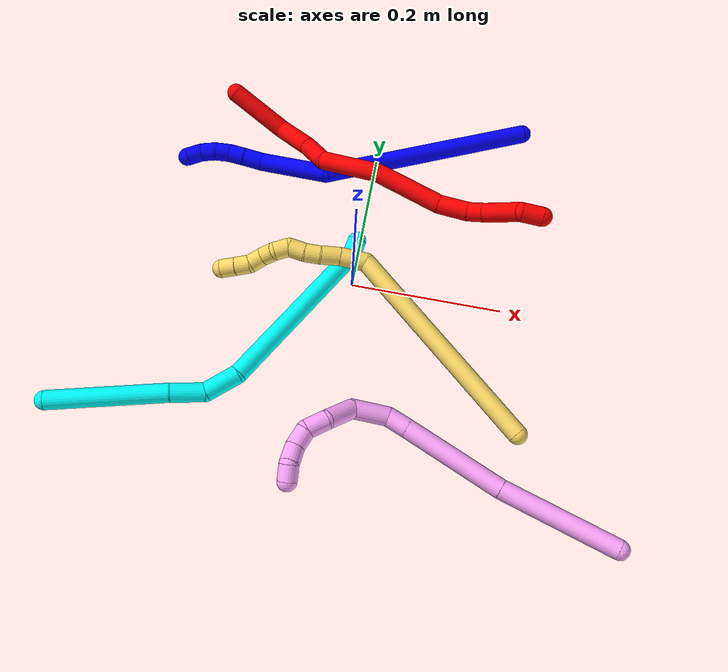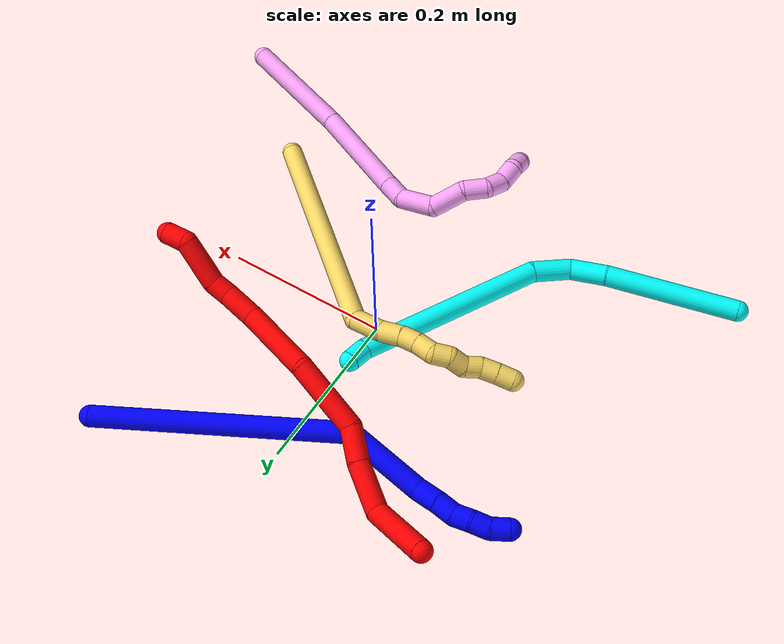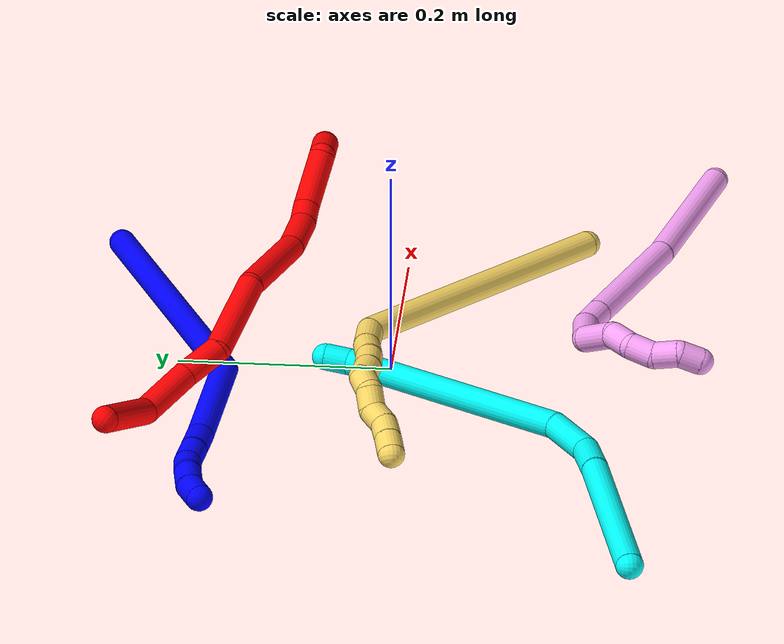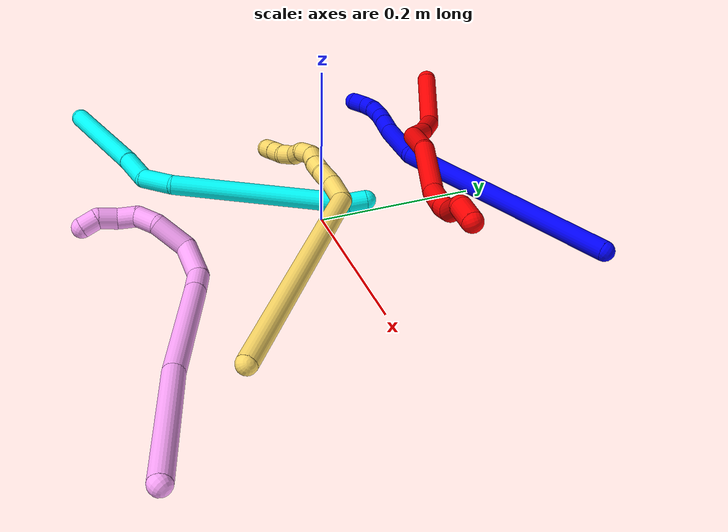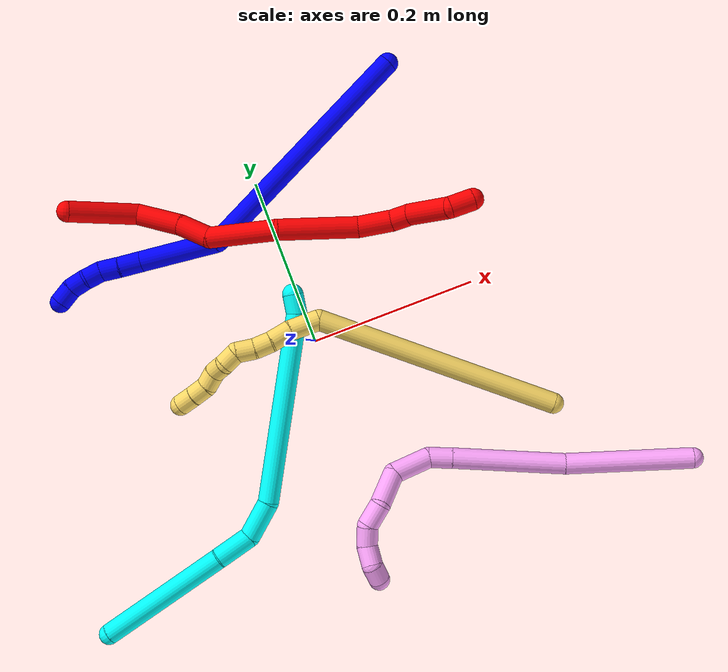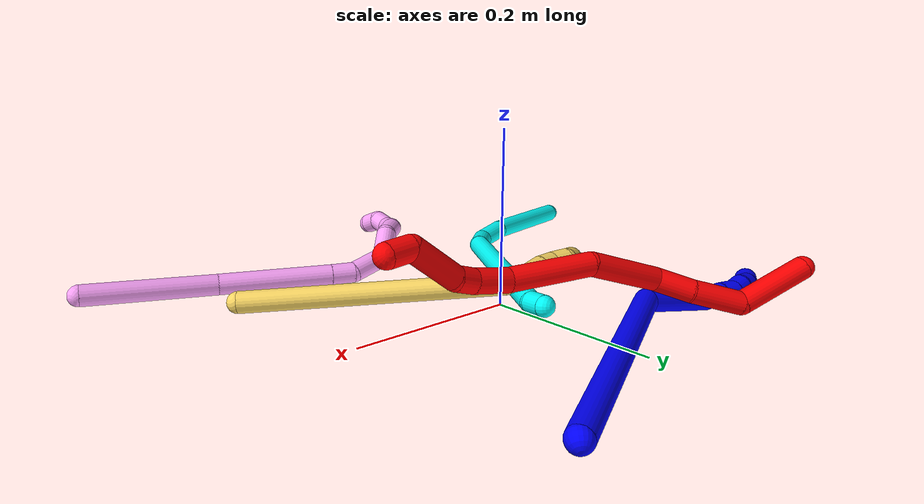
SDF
<sdf version="1.7">
 <world name="default">
  <plugin name="TubeGeneratorPlugin" filename="libtube_generator_plugin.so"/>
  <model name="photoneo_s_sensor">
   <static>1</static>
   <pose>0 0 2 1.57079 1.57079 3.14159</pose>
   <link name="link">
    <inertial><mass>0.1</mass></inertial>
    <sensor name="sensor" type="depth">
     <update_rate>30</update_rate>
     <camera>
      <horizontal_fov>1.22</horizontal_fov>
      <image><width>1920</width><height>1200</height><format>B8G8R8</format></image>
      <clip><near>0.1</near><far>4</far></clip>
      <depth_camera><output>points</output></depth_camera>
     </camera>
     <plugin name="camera_plugin" filename="libgazebo_ros_depth_camera.so">
      <baseline>0.2</baseline>
      <alwaysOn>1</alwaysOn>
      <updateRate>0.0</updateRate>
      <cameraName>camera_ir</cameraName>
      <imageTopicName>/camera/color/image_raw</imageTopicName>
      <cameraInfoTopicName>/camera/color/camera_info</cameraInfoTopicName>
      <depthImageTopicName>/camera/depth/image_raw</depthImageTopicName>
      <depthImageCameraInfoTopicName>/camera/depth/camera_info</depthImageCameraInfoTopicName>
      <pointCloudTopicName>/camera/depth/points</pointCloudTopicName>
      <frameName>fr_optical</frameName>
      <pointCloudCutoff>0.1</pointCloudCutoff>
      <pointCloudCutoffMax>2.0</pointCloudCutoffMax>
      <distortionK1>0</distortionK1>
      <distortionK2>0</distortionK2>
      <distortionK3>0</distortionK3>
      <distortionT1>0</distortionT1>
      <distortionT2>0</distortionT2>
      <CxPrime>0</CxPrime>
      <Cx>0</Cx>
      <Cy>0</Cy>
      <focalLength>0</focalLength>
      <hackBaseline>0</hackBaseline>
     </plugin>
    </sensor>
   </link>
  </model>
  <gravity>0 0 -9.8</gravity>
  <magnetic_field>6e-06 2.3e-05 -4.2e-05</magnetic_field>
  <atmosphere type="adiabatic"/>
  <physics name="default_physics" default="0" type="ode">
   <max_step_size>0.003</max_step_size>
   <real_time_factor>1</real_time_factor>
   <real_time_update_rate>1000</real_time_update_rate>
   <max_contacts>10000</max_contacts>
   <ode>
    <solver>
     <type>quick</type>
     <iters>100</iters>
     <sor>1.3</sor>
     <use_dynamic_moi_rescaling>0</use_dynamic_moi_rescaling>
    </solver>
    <constraints>
     <contact_max_correcting_vel>0</contact_max_correcting_vel>
     <contact_surface_layer>0.001</contact_surface_layer>
     <cfm>0</cfm>
     <erp>0.2</erp>
    </constraints>
   </ode>
  </physics>
  <scene><ambient>0.4 0.4 0.4 1</ambient><background>0.7 0.7 0.7 1</background><shadows>0</shadows></scene>
  <audio><device>default</device></audio>
  <spherical_coordinates>
   <surface_model>EARTH_WGS84</surface_model>
   <latitude_deg>0</latitude_deg>
   <longitude_deg>0</longitude_deg>
   <elevation>0</elevation>
   <heading_deg>0</heading_deg>
  </spherical_coordinates>
  <model name="bin">
   <static>1</static>
   <link name="bottom">
    <collision name="collision-bottom">
     <pose>0 0 -0.01 0 -0 0</pose>
     <geometry><box><size>0.8 0.6 0.02</size></box></geometry>
     <surface>
      <friction><ode><mu>100</mu><mu2>100</mu2></ode></friction>
      <contact><collide_bitmask>65535</collide_bitmask></contact>
     </surface>
    </collision>
   </link>
   <link name="west_wall">
    <collision name="collision-west_wall">
     <pose>-0.41 0 0.1 0 -0 0</pose>
     <geometry><box><size>0.02 0.6 0.2</size></box></geometry>
     <surface>
      <friction><ode><mu>100</mu><mu2>100</mu2></ode></friction>
      <contact><collide_bitmask>65535</collide_bitmask></contact>
     </surface>
    </collision>
   </link>
   <link name="east_wall">
    <collision name="collision-east_wall">
     <pose>0.41 0 0.1 0 -0 0</pose>
     <geometry><box><size>0.02 0.6 0.2</size></box></geometry>
     <surface>
      <friction><ode><mu>100</mu><mu2>100</mu2></ode></friction>
      <contact><collide_bitmask>65535</collide_bitmask></contact>
     </surface>
    </collision>
   </link>
   <link name="south_wall">
    <collision name="collision-south_wall">
     <pose>0 -0.31 0.1 0 -0 0</pose>
     <geometry><box><size>0.8 0.02 0.2</size></box></geometry>
     <surface>
      <friction><ode><mu>100</mu><mu2>100</mu2></ode></friction>
      <contact><collide_bitmask>65535</collide_bitmask></contact>
     </surface>
    </collision>
   </link>
   <link name="north_wall">
    <collision name="collision-north_wall">
     <pose>0 0.31 0.1 0 -0 0</pose>
     <geometry><box><size>0.8 0.02 0.2</size></box></geometry>
     <surface>
      <friction><ode><mu>100</mu><mu2>100</mu2></ode></friction>
      <contact><collide_bitmask>65535</collide_bitmask></contact>
     </surface>
    </collision>
   </link>
  </model>
  <model name="1">
   <static>0</static>
   <link name="1">
    <collision name="collision-cylinder-e_1_1_4">
     <pose>-0.075623 -0.041226 -0.117904 2.80522 -0.544417 -2.04864</pose>
     <geometry><cylinder><radius>0.0125</radius><length>0.292026</length></cylinder></geometry>
     <surface>
      <friction><ode><mu>1.16</mu><mu2>1.16</mu2><slip1>0</slip1><slip2>0</slip2></ode></friction>
      <contact><ode><kp>1e+06</kp><kd>1</kd><max_vel>0</max_vel><min_depth>0.001</min_depth></ode></contact>
     </surface>
    </collision>
    <visual name="visual-cylinder-e_1_1_4">
     <pose>-0.075623 -0.041226 -0.117904 2.80522 -0.544417 -2.04864</pose>
     <geometry><cylinder><radius>0.0125</radius><length>0.292026</length></cylinder></geometry>
     <material><ambient>0 0 1 1</ambient></material>
    </visual>
    <collision name="collision-cylinder-e_2_4_5">
     <pose>-0.181587 -0.115326 -0.253168 2.05667 -0.684514 -1.06763</pose>
     <geometry><cylinder><radius>0.0125</radius><length>0.09597</length></cylinder></geometry>
     <surface>
      <friction><ode><mu>1.16</mu><mu2>1.16</mu2><slip1>0</slip1><slip2>0</slip2></ode></friction>
      <contact><ode><kp>1e+06</kp><kd>1</kd><max_vel>0</max_vel><min_depth>0.001</min_depth></ode></contact>
     </surface>
    </collision>
    <visual name="visual-cylinder-e_2_4_5">
     <pose>-0.181587 -0.115326 -0.253168 2.05667 -0.684514 -1.06763</pose>
     <geometry><cylinder><radius>0.0125</radius><length>0.09597</length></cylinder></geometry>
     <material><ambient>0 0 1 1</ambient></material>
    </visual>
    <collision name="collision-cylinder-e_3_5_6">
     <pose>-0.218315 -0.158137 -0.27725 2.16553 -0.489207 -0.879018</pose>
     <geometry><cylinder><radius>0.0125</radius><length>0.027185</length></cylinder></geometry>
     <surface>
      <friction><ode><mu>1.16</mu><mu2>1.16</mu2><slip1>0</slip1><slip2>0</slip2></ode></friction>
      <contact><ode><kp>1e+06</kp><kd>1</kd><max_vel>0</max_vel><min_depth>0.001</min_depth></ode></contact>
     </surface>
    </collision>
    <visual name="visual-cylinder-e_3_5_6">
     <pose>-0.218315 -0.158137 -0.27725 2.16553 -0.489207 -0.879018</pose>
     <geometry><cylinder><radius>0.0125</radius><length>0.027185</length></cylinder></geometry>
     <material><ambient>0 0 1 1</ambient></material>
    </visual>
    <collision name="collision-cylinder-e_4_6_7">
     <pose>-0.23077 -0.176356 -0.28873 2.09227 -0.566 -0.931222</pose>
     <geometry><cylinder><radius>0.0125</radius><length>0.022628</length></cylinder></geometry>
     <surface>
      <friction><ode><mu>1.16</mu><mu2>1.16</mu2><slip1>0</slip1><slip2>0</slip2></ode></friction>
      <contact><ode><kp>1e+06</kp><kd>1</kd><max_vel>0</max_vel><min_depth>0.001</min_depth></ode></contact>
     </surface>
    </collision>
    <visual name="visual-cylinder-e_4_6_7">
     <pose>-0.23077 -0.176356 -0.28873 2.09227 -0.566 -0.931222</pose>
     <geometry><cylinder><radius>0.0125</radius><length>0.022628</length></cylinder></geometry>
     <material><ambient>0 0 1 1</ambient></material>
    </visual>
    <collision name="collision-cylinder-e_5_7_8">
     <pose>-0.241462 -0.190544 -0.300319 2.42859 -0.473254 -1.14925</pose>
     <geometry><cylinder><radius>0.0125</radius><length>0.020296</length></cylinder></geometry>
     <surface>
      <friction><ode><mu>1.16</mu><mu2>1.16</mu2><slip1>0</slip1><slip2>0</slip2></ode></friction>
      <contact><ode><kp>1e+06</kp><kd>1</kd><max_vel>0</max_vel><min_depth>0.001</min_depth></ode></contact>
     </surface>
    </collision>
    <visual name="visual-cylinder-e_5_7_8">
     <pose>-0.241462 -0.190544 -0.300319 2.42859 -0.473254 -1.14925</pose>
     <geometry><cylinder><radius>0.0125</radius><length>0.020296</length></cylinder></geometry>
     <material><ambient>0 0 1 1</ambient></material>
    </visual>
    <collision name="collision-cylinder-e_6_8_9">
     <pose>-0.252862 -0.201232 -0.313165 2.47 -0.722709 -1.65036</pose>
     <geometry><cylinder><radius>0.0125</radius><length>0.020484</length></cylinder></geometry>
     <surface>
      <friction><ode><mu>1.16</mu><mu2>1.16</mu2><slip1>0</slip1><slip2>0</slip2></ode></friction>
      <contact><ode><kp>1e+06</kp><kd>1</kd><max_vel>0</max_vel><min_depth>0.001</min_depth></ode></contact>
     </surface>
    </collision>
    <visual name="visual-cylinder-e_6_8_9">
     <pose>-0.252862 -0.201232 -0.313165 2.47 -0.722709 -1.65036</pose>
     <geometry><cylinder><radius>0.0125</radius><length>0.020484</length></cylinder></geometry>
     <material><ambient>0 0 1 1</ambient></material>
    </visual>
    <collision name="collision-cylinder-e_7_9_2">
     <pose>-0.265823 -0.208106 -0.327661 2.89963 -0.616109 -2.41164</pose>
     <geometry><cylinder><radius>0.0125</radius><length>0.021411</length></cylinder></geometry>
     <surface>
      <friction><ode><mu>1.16</mu><mu2>1.16</mu2><slip1>0</slip1><slip2>0</slip2></ode></friction>
      <contact><ode><kp>1e+06</kp><kd>1</kd><max_vel>0</max_vel><min_depth>0.001</min_depth></ode></contact>
     </surface>
    </collision>
    <visual name="visual-cylinder-e_7_9_2">
     <pose>-0.265823 -0.208106 -0.327661 2.89963 -0.616109 -2.41164</pose>
     <geometry><cylinder><radius>0.0125</radius><length>0.021411</length></cylinder></geometry>
     <material><ambient>0 0 1 1</ambient></material>
    </visual>
    <collision name="collision-sphere-2">
     <pose>-0.272009 -0.210199 -0.336144 0 -0 0</pose>
     <geometry><sphere><radius>0.0125</radius></sphere></geometry>
     <surface>
      <friction><ode><mu>1.16</mu><mu2>1.16</mu2><slip1>0</slip1><slip2>0</slip2></ode></friction>
      <contact><ode><kp>1e+06</kp><kd>1</kd><max_vel>0</max_vel><min_depth>0.001</min_depth></ode></contact>
     </surface>
    </collision>
    <visual name="visual-sphere-2">
     <pose>-0.272009 -0.210199 -0.336144 0 -0 0</pose>
     <geometry><sphere><radius>0.0125</radius></sphere></geometry>
     <material><ambient>0 0 1 1</ambient></material>
    </visual>
    <collision name="collision-sphere-9">
     <pose>-0.259636 -0.206012 -0.319179 0 -0 0</pose>
     <geometry><sphere><radius>0.0125</radius></sphere></geometry>
     <surface>
      <friction><ode><mu>1.16</mu><mu2>1.16</mu2><slip1>0</slip1><slip2>0</slip2></ode></friction>
      <contact><ode><kp>1e+06</kp><kd>1</kd><max_vel>0</max_vel><min_depth>0.001</min_depth></ode></contact>
     </surface>
    </collision>
    <visual name="visual-sphere-9">
     <pose>-0.259636 -0.206012 -0.319179 0 -0 0</pose>
     <geometry><sphere><radius>0.0125</radius></sphere></geometry>
     <material><ambient>0 0 1 1</ambient></material>
    </visual>
    <collision name="collision-sphere-4">
     <pose>-0.151246 -0.082453 -0.235807 0 -0 0</pose>
     <geometry><sphere><radius>0.0125</radius></sphere></geometry>
     <surface>
      <friction><ode><mu>1.16</mu><mu2>1.16</mu2><slip1>0</slip1><slip2>0</slip2></ode></friction>
      <contact><ode><kp>1e+06</kp><kd>1</kd><max_vel>0</max_vel><min_depth>0.001</min_depth></ode></contact>
     </surface>
    </collision>
    <visual name="visual-sphere-4">
     <pose>-0.151246 -0.082453 -0.235807 0 -0 0</pose>
     <geometry><sphere><radius>0.0125</radius></sphere></geometry>
     <material><ambient>0 0 1 1</ambient></material>
    </visual>
    <collision name="collision-sphere-1">
     <geometry><sphere><radius>0.0125</radius></sphere></geometry>
     <surface>
      <friction><ode><mu>1.16</mu><mu2>1.16</mu2><slip1>0</slip1><slip2>0</slip2></ode></friction>
      <contact><ode><kp>1e+06</kp><kd>1</kd><max_vel>0</max_vel><min_depth>0.001</min_depth></ode></contact>
     </surface>
    </collision>
    <visual name="visual-sphere-1">
     <geometry><sphere><radius>0.0125</radius></sphere></geometry>
     <material><ambient>0 0 1 1</ambient></material>
    </visual>
    <collision name="collision-sphere-8">
     <pose>-0.246088 -0.196453 -0.307152 0 -0 0</pose>
     <geometry><sphere><radius>0.0125</radius></sphere></geometry>
     <surface>
      <friction><ode><mu>1.16</mu><mu2>1.16</mu2><slip1>0</slip1><slip2>0</slip2></ode></friction>
      <contact><ode><kp>1e+06</kp><kd>1</kd><max_vel>0</max_vel><min_depth>0.001</min_depth></ode></contact>
     </surface>
    </collision>
    <visual name="visual-sphere-8">
     <pose>-0.246088 -0.196453 -0.307152 0 -0 0</pose>
     <geometry><sphere><radius>0.0125</radius></sphere></geometry>
     <material><ambient>0 0 1 1</ambient></material>
    </visual>
    <collision name="collision-sphere-5">
     <pose>-0.211928 -0.148199 -0.270528 0 -0 0</pose>
     <geometry><sphere><radius>0.0125</radius></sphere></geometry>
     <surface>
      <friction><ode><mu>1.16</mu><mu2>1.16</mu2><slip1>0</slip1><slip2>0</slip2></ode></friction>
      <contact><ode><kp>1e+06</kp><kd>1</kd><max_vel>0</max_vel><min_depth>0.001</min_depth></ode></contact>
     </surface>
    </collision>
    <visual name="visual-sphere-5">
     <pose>-0.211928 -0.148199 -0.270528 0 -0 0</pose>
     <geometry><sphere><radius>0.0125</radius></sphere></geometry>
     <material><ambient>0 0 1 1</ambient></material>
    </visual>
    <collision name="collision-sphere-6">
     <pose>-0.224703 -0.168075 -0.283973 0 -0 0</pose>
     <geometry><sphere><radius>0.0125</radius></sphere></geometry>
     <surface>
      <friction><ode><mu>1.16</mu><mu2>1.16</mu2><slip1>0</slip1><slip2>0</slip2></ode></friction>
      <contact><ode><kp>1e+06</kp><kd>1</kd><max_vel>0</max_vel><min_depth>0.001</min_depth></ode></contact>
     </surface>
    </collision>
    <visual name="visual-sphere-6">
     <pose>-0.224703 -0.168075 -0.283973 0 -0 0</pose>
     <geometry><sphere><radius>0.0125</radius></sphere></geometry>
     <material><ambient>0 0 1 1</ambient></material>
    </visual>
    <collision name="collision-sphere-7">
     <pose>-0.236837 -0.184636 -0.293487 0 -0 0</pose>
     <geometry><sphere><radius>0.0125</radius></sphere></geometry>
     <surface>
      <friction><ode><mu>1.16</mu><mu2>1.16</mu2><slip1>0</slip1><slip2>0</slip2></ode></friction>
      <contact><ode><kp>1e+06</kp><kd>1</kd><max_vel>0</max_vel><min_depth>0.001</min_depth></ode></contact>
     </surface>
    </collision>
    <visual name="visual-sphere-7">
     <pose>-0.236837 -0.184636 -0.293487 0 -0 0</pose>
     <geometry><sphere><radius>0.0125</radius></sphere></geometry>
     <material><ambient>0 0 1 1</ambient></material>
    </visual>
    <inertial>
     <pose>-0.132879 -0.087683 -0.184647 0 -0 0</pose>
     <mass>0.5</mass>
     <inertia>
      <ixx>-0.002455</ixx>
      <ixy>0</ixy>
      <ixz>0</ixz>
      <iyy>-0.000415</iyy>
      <iyz>0</iyz>
      <izz>0.001756</izz>
     </inertia>
    </inertial>
   </link>
   <pose>0.197516 0.27701 0.016604 -2.67856 -0.976727 0.346379</pose>
  </model>
  <model name="2">
   <static>0</static>
   <link name="2">
    <collision name="collision-cylinder-e_1_1_4">
     <pose>0.03954 0.009097 -0.006159 -2.16599 1.2998 -1.92273</pose>
     <geometry><cylinder><radius>0.0125</radius><length>0.082076</length></cylinder></geometry>
     <surface>
      <friction><ode><mu>1.16</mu><mu2>1.16</mu2><slip1>0</slip1><slip2>0</slip2></ode></friction>
      <contact><ode><kp>1e+06</kp><kd>1</kd><max_vel>0</max_vel><min_depth>0.001</min_depth></ode></contact>
     </surface>
    </collision>
    <visual name="visual-cylinder-e_1_1_4">
     <pose>0.03954 0.009097 -0.006159 -2.16599 1.2998 -1.92273</pose>
     <geometry><cylinder><radius>0.0125</radius><length>0.082076</length></cylinder></geometry>
     <material><ambient>1 0 0 1</ambient></material>
    </visual>
    <collision name="collision-cylinder-e_2_4_5">
     <pose>0.104141 0.00524 -0.014593 1.74461 1.08751 1.24797</pose>
     <geometry><cylinder><radius>0.0125</radius><length>0.056603</length></cylinder></geometry>
     <surface>
      <friction><ode><mu>1.16</mu><mu2>1.16</mu2><slip1>0</slip1><slip2>0</slip2></ode></friction>
      <contact><ode><kp>1e+06</kp><kd>1</kd><max_vel>0</max_vel><min_depth>0.001</min_depth></ode></contact>
     </surface>
    </collision>
    <visual name="visual-cylinder-e_2_4_5">
     <pose>0.104141 0.00524 -0.014593 1.74461 1.08751 1.24797</pose>
     <geometry><cylinder><radius>0.0125</radius><length>0.056603</length></cylinder></geometry>
     <material><ambient>1 0 0 1</ambient></material>
    </visual>
    <collision name="collision-cylinder-e_3_5_6">
     <pose>0.14551 -0.018873 -0.020625 1.89563 0.945479 1.23729</pose>
     <geometry><cylinder><radius>0.0125</radius><length>0.040232</length></cylinder></geometry>
     <surface>
      <friction><ode><mu>1.16</mu><mu2>1.16</mu2><slip1>0</slip1><slip2>0</slip2></ode></friction>
      <contact><ode><kp>1e+06</kp><kd>1</kd><max_vel>0</max_vel><min_depth>0.001</min_depth></ode></contact>
     </surface>
    </collision>
    <visual name="visual-cylinder-e_3_5_6">
     <pose>0.14551 -0.018873 -0.020625 1.89563 0.945479 1.23729</pose>
     <geometry><cylinder><radius>0.0125</radius><length>0.040232</length></cylinder></geometry>
     <material><ambient>1 0 0 1</ambient></material>
    </visual>
    <collision name="collision-cylinder-e_4_6_7">
     <pose>0.200514 -0.04499 -0.014412 0.982848 1.13587 0.658167</pose>
     <geometry><cylinder><radius>0.0125</radius><length>0.085333</length></cylinder></geometry>
     <surface>
      <friction><ode><mu>1.16</mu><mu2>1.16</mu2><slip1>0</slip1><slip2>0</slip2></ode></friction>
      <contact><ode><kp>1e+06</kp><kd>1</kd><max_vel>0</max_vel><min_depth>0.001</min_depth></ode></contact>
     </surface>
    </collision>
    <visual name="visual-cylinder-e_4_6_7">
     <pose>0.200514 -0.04499 -0.014412 0.982848 1.13587 0.658167</pose>
     <geometry><cylinder><radius>0.0125</radius><length>0.085333</length></cylinder></geometry>
     <material><ambient>1 0 0 1</ambient></material>
    </visual>
    <collision name="collision-cylinder-e_5_7_8">
     <pose>0.28506 -0.062121 -0.003018 0.99075 1.51421 0.944137</pose>
     <geometry><cylinder><radius>0.0125</radius><length>0.091851</length></cylinder></geometry>
     <surface>
      <friction><ode><mu>1.16</mu><mu2>1.16</mu2><slip1>0</slip1><slip2>0</slip2></ode></friction>
      <contact><ode><kp>1e+06</kp><kd>1</kd><max_vel>0</max_vel><min_depth>0.001</min_depth></ode></contact>
     </surface>
    </collision>
    <visual name="visual-cylinder-e_5_7_8">
     <pose>0.28506 -0.062121 -0.003018 0.99075 1.51421 0.944137</pose>
     <geometry><cylinder><radius>0.0125</radius><length>0.091851</length></cylinder></geometry>
     <material><ambient>1 0 0 1</ambient></material>
    </visual>
    <collision name="collision-cylinder-e_6_8_9">
     <pose>0.349955 -0.067475 0.003178 0.588057 1.27825 0.442705</pose>
     <geometry><cylinder><radius>0.0125</radius><length>0.039776</length></cylinder></geometry>
     <surface>
      <friction><ode><mu>1.16</mu><mu2>1.16</mu2><slip1>0</slip1><slip2>0</slip2></ode></friction>
      <contact><ode><kp>1e+06</kp><kd>1</kd><max_vel>0</max_vel><min_depth>0.001</min_depth></ode></contact>
     </surface>
    </collision>
    <visual name="visual-cylinder-e_6_8_9">
     <pose>0.349955 -0.067475 0.003178 0.588057 1.27825 0.442705</pose>
     <geometry><cylinder><radius>0.0125</radius><length>0.039776</length></cylinder></geometry>
     <material><ambient>1 0 0 1</ambient></material>
    </visual>
    <collision name="collision-cylinder-e_7_9_10">
     <pose>0.378534 -0.073259 0.012423 0.526815 1.07363 0.318256</pose>
     <geometry><cylinder><radius>0.0125</radius><length>0.0217</length></cylinder></geometry>
     <surface>
      <friction><ode><mu>1.16</mu><mu2>1.16</mu2><slip1>0</slip1><slip2>0</slip2></ode></friction>
      <contact><ode><kp>1e+06</kp><kd>1</kd><max_vel>0</max_vel><min_depth>0.001</min_depth></ode></contact>
     </surface>
    </collision>
    <visual name="visual-cylinder-e_7_9_10">
     <pose>0.378534 -0.073259 0.012423 0.526815 1.07363 0.318256</pose>
     <geometry><cylinder><radius>0.0125</radius><length>0.0217</length></cylinder></geometry>
     <material><ambient>1 0 0 1</ambient></material>
    </visual>
    <collision name="collision-cylinder-e_8_10_11">
     <pose>0.40748 -0.092549 0.026998 1.02649 0.782901 0.457146</pose>
     <geometry><cylinder><radius>0.0125</radius><length>0.055037</length></cylinder></geometry>
     <surface>
      <friction><ode><mu>1.16</mu><mu2>1.16</mu2><slip1>0</slip1><slip2>0</slip2></ode></friction>
      <contact><ode><kp>1e+06</kp><kd>1</kd><max_vel>0</max_vel><min_depth>0.001</min_depth></ode></contact>
     </surface>
    </collision>
    <visual name="visual-cylinder-e_8_10_11">
     <pose>0.40748 -0.092549 0.026998 1.02649 0.782901 0.457146</pose>
     <geometry><cylinder><radius>0.0125</radius><length>0.055037</length></cylinder></geometry>
     <material><ambient>1 0 0 1</ambient></material>
    </visual>
    <collision name="collision-cylinder-e_9_11_2">
     <pose>0.439907 -0.107681 0.041065 -0.373824 1.25452 -0.272498</pose>
     <geometry><cylinder><radius>0.0125</radius><length>0.027393</length></cylinder></geometry>
     <surface>
      <friction><ode><mu>1.16</mu><mu2>1.16</mu2><slip1>0</slip1><slip2>0</slip2></ode></friction>
      <contact><ode><kp>1e+06</kp><kd>1</kd><max_vel>0</max_vel><min_depth>0.001</min_depth></ode></contact>
     </surface>
    </collision>
    <visual name="visual-cylinder-e_9_11_2">
     <pose>0.439907 -0.107681 0.041065 -0.373824 1.25452 -0.272498</pose>
     <geometry><cylinder><radius>0.0125</radius><length>0.027393</length></cylinder></geometry>
     <material><ambient>1 0 0 1</ambient></material>
    </visual>
    <collision name="collision-sphere-2">
     <pose>0.452925 -0.106126 0.04503 0 -0 0</pose>
     <geometry><sphere><radius>0.0125</radius></sphere></geometry>
     <surface>
      <friction><ode><mu>1.16</mu><mu2>1.16</mu2><slip1>0</slip1><slip2>0</slip2></ode></friction>
      <contact><ode><kp>1e+06</kp><kd>1</kd><max_vel>0</max_vel><min_depth>0.001</min_depth></ode></contact>
     </surface>
    </collision>
    <visual name="visual-sphere-2">
     <pose>0.452925 -0.106126 0.04503 0 -0 0</pose>
     <geometry><sphere><radius>0.0125</radius></sphere></geometry>
     <material><ambient>1 0 0 1</ambient></material>
    </visual>
    <collision name="collision-sphere-11">
     <pose>0.42689 -0.109237 0.037099 0 -0 0</pose>
     <geometry><sphere><radius>0.0125</radius></sphere></geometry>
     <surface>
      <friction><ode><mu>1.16</mu><mu2>1.16</mu2><slip1>0</slip1><slip2>0</slip2></ode></friction>
      <contact><ode><kp>1e+06</kp><kd>1</kd><max_vel>0</max_vel><min_depth>0.001</min_depth></ode></contact>
     </surface>
    </collision>
    <visual name="visual-sphere-11">
     <pose>0.42689 -0.109237 0.037099 0 -0 0</pose>
     <geometry><sphere><radius>0.0125</radius></sphere></geometry>
     <material><ambient>1 0 0 1</ambient></material>
    </visual>
    <collision name="collision-sphere-10">
     <pose>0.38807 -0.075861 0.016896 0 -0 0</pose>
     <geometry><sphere><radius>0.0125</radius></sphere></geometry>
     <surface>
      <friction><ode><mu>1.16</mu><mu2>1.16</mu2><slip1>0</slip1><slip2>0</slip2></ode></friction>
      <contact><ode><kp>1e+06</kp><kd>1</kd><max_vel>0</max_vel><min_depth>0.001</min_depth></ode></contact>
     </surface>
    </collision>
    <visual name="visual-sphere-10">
     <pose>0.38807 -0.075861 0.016896 0 -0 0</pose>
     <geometry><sphere><radius>0.0125</radius></sphere></geometry>
     <material><ambient>1 0 0 1</ambient></material>
    </visual>
    <collision name="collision-sphere-9">
     <pose>0.368997 -0.070657 0.00795 0 -0 0</pose>
     <geometry><sphere><radius>0.0125</radius></sphere></geometry>
     <surface>
      <friction><ode><mu>1.16</mu><mu2>1.16</mu2><slip1>0</slip1><slip2>0</slip2></ode></friction>
      <contact><ode><kp>1e+06</kp><kd>1</kd><max_vel>0</max_vel><min_depth>0.001</min_depth></ode></contact>
     </surface>
    </collision>
    <visual name="visual-sphere-9">
     <pose>0.368997 -0.070657 0.00795 0 -0 0</pose>
     <geometry><sphere><radius>0.0125</radius></sphere></geometry>
     <material><ambient>1 0 0 1</ambient></material>
    </visual>
    <collision name="collision-sphere-4">
     <pose>0.07908 0.018193 -0.012319 0 -0 0</pose>
     <geometry><sphere><radius>0.0125</radius></sphere></geometry>
     <surface>
      <friction><ode><mu>1.16</mu><mu2>1.16</mu2><slip1>0</slip1><slip2>0</slip2></ode></friction>
      <contact><ode><kp>1e+06</kp><kd>1</kd><max_vel>0</max_vel><min_depth>0.001</min_depth></ode></contact>
     </surface>
    </collision>
    <visual name="visual-sphere-4">
     <pose>0.07908 0.018193 -0.012319 0 -0 0</pose>
     <geometry><sphere><radius>0.0125</radius></sphere></geometry>
     <material><ambient>1 0 0 1</ambient></material>
    </visual>
    <collision name="collision-sphere-1">
     <geometry><sphere><radius>0.0125</radius></sphere></geometry>
     <surface>
      <friction><ode><mu>1.16</mu><mu2>1.16</mu2><slip1>0</slip1><slip2>0</slip2></ode></friction>
      <contact><ode><kp>1e+06</kp><kd>1</kd><max_vel>0</max_vel><min_depth>0.001</min_depth></ode></contact>
     </surface>
    </collision>
    <visual name="visual-sphere-1">
     <geometry><sphere><radius>0.0125</radius></sphere></geometry>
     <material><ambient>1 0 0 1</ambient></material>
    </visual>
    <collision name="collision-sphere-8">
     <pose>0.330912 -0.064294 -0.001594 0 -0 0</pose>
     <geometry><sphere><radius>0.0125</radius></sphere></geometry>
     <surface>
      <friction><ode><mu>1.16</mu><mu2>1.16</mu2><slip1>0</slip1><slip2>0</slip2></ode></friction>
      <contact><ode><kp>1e+06</kp><kd>1</kd><max_vel>0</max_vel><min_depth>0.001</min_depth></ode></contact>
     </surface>
    </collision>
    <visual name="visual-sphere-8">
     <pose>0.330912 -0.064294 -0.001594 0 -0 0</pose>
     <geometry><sphere><radius>0.0125</radius></sphere></geometry>
     <material><ambient>1 0 0 1</ambient></material>
    </visual>
    <collision name="collision-sphere-5">
     <pose>0.129201 -0.007713 -0.016867 0 -0 0</pose>
     <geometry><sphere><radius>0.0125</radius></sphere></geometry>
     <surface>
      <friction><ode><mu>1.16</mu><mu2>1.16</mu2><slip1>0</slip1><slip2>0</slip2></ode></friction>
      <contact><ode><kp>1e+06</kp><kd>1</kd><max_vel>0</max_vel><min_depth>0.001</min_depth></ode></contact>
     </surface>
    </collision>
    <visual name="visual-sphere-5">
     <pose>0.129201 -0.007713 -0.016867 0 -0 0</pose>
     <geometry><sphere><radius>0.0125</radius></sphere></geometry>
     <material><ambient>1 0 0 1</ambient></material>
    </visual>
    <collision name="collision-sphere-6">
     <pose>0.16182 -0.030032 -0.024383 0 -0 0</pose>
     <geometry><sphere><radius>0.0125</radius></sphere></geometry>
     <surface>
      <friction><ode><mu>1.16</mu><mu2>1.16</mu2><slip1>0</slip1><slip2>0</slip2></ode></friction>
      <contact><ode><kp>1e+06</kp><kd>1</kd><max_vel>0</max_vel><min_depth>0.001</min_depth></ode></contact>
     </surface>
    </collision>
    <visual name="visual-sphere-6">
     <pose>0.16182 -0.030032 -0.024383 0 -0 0</pose>
     <geometry><sphere><radius>0.0125</radius></sphere></geometry>
     <material><ambient>1 0 0 1</ambient></material>
    </visual>
    <collision name="collision-sphere-7">
     <pose>0.239208 -0.059949 -0.004441 0 -0 0</pose>
     <geometry><sphere><radius>0.0125</radius></sphere></geometry>
     <surface>
      <friction><ode><mu>1.16</mu><mu2>1.16</mu2><slip1>0</slip1><slip2>0</slip2></ode></friction>
      <contact><ode><kp>1e+06</kp><kd>1</kd><max_vel>0</max_vel><min_depth>0.001</min_depth></ode></contact>
     </surface>
    </collision>
    <visual name="visual-sphere-7">
     <pose>0.239208 -0.059949 -0.004441 0 -0 0</pose>
     <geometry><sphere><radius>0.0125</radius></sphere></geometry>
     <material><ambient>1 0 0 1</ambient></material>
    </visual>
    <inertial>
     <pose>0.229797 -0.043156 -0.001323 0 -0 0</pose>
     <mass>0.5</mass>
     <inertia>
      <ixx>9.1e-05</ixx>
      <ixy>0</ixy>
      <ixz>0</ixz>
      <iyy>0.000219</iyy>
      <iyz>0</iyz>
      <izz>-0.000171</izz>
     </inertia>
    </inertial>
   </link>
   <pose>-0.212079 0.239916 0.057292 -1.09495 0.118607 -0.328464</pose>
  </model>
  <model name="3">
   <static>0</static>
   <link name="3">
    <collision name="collision-cylinder-e_1_1_4">
     <pose>-0.002628 -0.004369 0.010788 0.384826 -0.222079 -0.043438</pose>
     <geometry><cylinder><radius>0.0125</radius><length>0.023864</length></cylinder></geometry>
     <surface>
      <friction><ode><mu>1.16</mu><mu2>1.16</mu2><slip1>0</slip1><slip2>0</slip2></ode></friction>
      <contact><ode><kp>1e+06</kp><kd>1</kd><max_vel>0</max_vel><min_depth>0.001</min_depth></ode></contact>
     </surface>
    </collision>
    <visual name="visual-cylinder-e_1_1_4">
     <pose>-0.002628 -0.004369 0.010788 0.384826 -0.222079 -0.043438</pose>
     <geometry><cylinder><radius>0.0125</radius><length>0.023864</length></cylinder></geometry>
     <material><ambient>0.003922 1 0.996078 1</ambient></material>
    </visual>
    <collision name="collision-cylinder-e_2_4_5">
     <pose>-0.056091 -0.07068 0.101335 0.660307 -0.466347 -0.162418</pose>
     <geometry><cylinder><radius>0.0125</radius><length>0.226119</length></cylinder></geometry>
     <surface>
      <friction><ode><mu>1.16</mu><mu2>1.16</mu2><slip1>0</slip1><slip2>0</slip2></ode></friction>
      <contact><ode><kp>1e+06</kp><kd>1</kd><max_vel>0</max_vel><min_depth>0.001</min_depth></ode></contact>
     </surface>
    </collision>
    <visual name="visual-cylinder-e_2_4_5">
     <pose>-0.056091 -0.07068 0.101335 0.660307 -0.466347 -0.162418</pose>
     <geometry><cylinder><radius>0.0125</radius><length>0.226119</length></cylinder></geometry>
     <material><ambient>0.003922 1 0.996078 1</ambient></material>
    </visual>
    <collision name="collision-cylinder-e_3_5_6">
     <pose>-0.117378 -0.151055 0.191148 1.07155 -0.461898 -0.277418</pose>
     <geometry><cylinder><radius>0.0125</radius><length>0.04691</length></cylinder></geometry>
     <surface>
      <friction><ode><mu>1.16</mu><mu2>1.16</mu2><slip1>0</slip1><slip2>0</slip2></ode></friction>
      <contact><ode><kp>1e+06</kp><kd>1</kd><max_vel>0</max_vel><min_depth>0.001</min_depth></ode></contact>
     </surface>
    </collision>
    <visual name="visual-cylinder-e_3_5_6">
     <pose>-0.117378 -0.151055 0.191148 1.07155 -0.461898 -0.277418</pose>
     <geometry><cylinder><radius>0.0125</radius><length>0.04691</length></cylinder></geometry>
     <material><ambient>0.003922 1 0.996078 1</ambient></material>
    </visual>
    <collision name="collision-cylinder-e_4_6_7">
     <pose>-0.14179 -0.186798 0.200405 1.61669 -0.678169 -0.707486</pose>
     <geometry><cylinder><radius>0.0125</radius><length>0.044501</length></cylinder></geometry>
     <surface>
      <friction><ode><mu>1.16</mu><mu2>1.16</mu2><slip1>0</slip1><slip2>0</slip2></ode></friction>
      <contact><ode><kp>1e+06</kp><kd>1</kd><max_vel>0</max_vel><min_depth>0.001</min_depth></ode></contact>
     </surface>
    </collision>
    <visual name="visual-cylinder-e_4_6_7">
     <pose>-0.14179 -0.186798 0.200405 1.61669 -0.678169 -0.707486</pose>
     <geometry><cylinder><radius>0.0125</radius><length>0.044501</length></cylinder></geometry>
     <material><ambient>0.003922 1 0.996078 1</ambient></material>
    </visual>
    <collision name="collision-cylinder-e_5_7_2">
     <pose>-0.196312 -0.272227 0.197794 1.59746 -0.536912 -0.550709</pose>
     <geometry><cylinder><radius>0.0125</radius><length>0.158605</length></cylinder></geometry>
     <surface>
      <friction><ode><mu>1.16</mu><mu2>1.16</mu2><slip1>0</slip1><slip2>0</slip2></ode></friction>
      <contact><ode><kp>1e+06</kp><kd>1</kd><max_vel>0</max_vel><min_depth>0.001</min_depth></ode></contact>
     </surface>
    </collision>
    <visual name="visual-cylinder-e_5_7_2">
     <pose>-0.196312 -0.272227 0.197794 1.59746 -0.536912 -0.550709</pose>
     <geometry><cylinder><radius>0.0125</radius><length>0.158605</length></cylinder></geometry>
     <material><ambient>0.003922 1 0.996078 1</ambient></material>
    </visual>
    <collision name="collision-sphere-2">
     <pose>-0.236874 -0.340347 0.195977 0 -0 0</pose>
     <geometry><sphere><radius>0.0125</radius></sphere></geometry>
     <surface>
      <friction><ode><mu>1.16</mu><mu2>1.16</mu2><slip1>0</slip1><slip2>0</slip2></ode></friction>
      <contact><ode><kp>1e+06</kp><kd>1</kd><max_vel>0</max_vel><min_depth>0.001</min_depth></ode></contact>
     </surface>
    </collision>
    <visual name="visual-sphere-2">
     <pose>-0.236874 -0.340347 0.195977 0 -0 0</pose>
     <geometry><sphere><radius>0.0125</radius></sphere></geometry>
     <material><ambient>0.003922 1 0.996078 1</ambient></material>
    </visual>
    <collision name="collision-sphere-7">
     <pose>-0.15575 -0.204107 0.199611 0 -0 0</pose>
     <geometry><sphere><radius>0.0125</radius></sphere></geometry>
     <surface>
      <friction><ode><mu>1.16</mu><mu2>1.16</mu2><slip1>0</slip1><slip2>0</slip2></ode></friction>
      <contact><ode><kp>1e+06</kp><kd>1</kd><max_vel>0</max_vel><min_depth>0.001</min_depth></ode></contact>
     </surface>
    </collision>
    <visual name="visual-sphere-7">
     <pose>-0.15575 -0.204107 0.199611 0 -0 0</pose>
     <geometry><sphere><radius>0.0125</radius></sphere></geometry>
     <material><ambient>0.003922 1 0.996078 1</ambient></material>
    </visual>
    <collision name="collision-sphere-6">
     <pose>-0.127831 -0.169489 0.2012 0 -0 0</pose>
     <geometry><sphere><radius>0.0125</radius></sphere></geometry>
     <surface>
      <friction><ode><mu>1.16</mu><mu2>1.16</mu2><slip1>0</slip1><slip2>0</slip2></ode></friction>
      <contact><ode><kp>1e+06</kp><kd>1</kd><max_vel>0</max_vel><min_depth>0.001</min_depth></ode></contact>
     </surface>
    </collision>
    <visual name="visual-sphere-6">
     <pose>-0.127831 -0.169489 0.2012 0 -0 0</pose>
     <geometry><sphere><radius>0.0125</radius></sphere></geometry>
     <material><ambient>0.003922 1 0.996078 1</ambient></material>
    </visual>
    <collision name="collision-sphere-5">
     <pose>-0.106925 -0.13262 0.181095 0 -0 0</pose>
     <geometry><sphere><radius>0.0125</radius></sphere></geometry>
     <surface>
      <friction><ode><mu>1.16</mu><mu2>1.16</mu2><slip1>0</slip1><slip2>0</slip2></ode></friction>
      <contact><ode><kp>1e+06</kp><kd>1</kd><max_vel>0</max_vel><min_depth>0.001</min_depth></ode></contact>
     </surface>
    </collision>
    <visual name="visual-sphere-5">
     <pose>-0.106925 -0.13262 0.181095 0 -0 0</pose>
     <geometry><sphere><radius>0.0125</radius></sphere></geometry>
     <material><ambient>0.003922 1 0.996078 1</ambient></material>
    </visual>
    <collision name="collision-sphere-1">
     <geometry><sphere><radius>0.0125</radius></sphere></geometry>
     <surface>
      <friction><ode><mu>1.16</mu><mu2>1.16</mu2><slip1>0</slip1><slip2>0</slip2></ode></friction>
      <contact><ode><kp>1e+06</kp><kd>1</kd><max_vel>0</max_vel><min_depth>0.001</min_depth></ode></contact>
     </surface>
    </collision>
    <visual name="visual-sphere-1">
     <geometry><sphere><radius>0.0125</radius></sphere></geometry>
     <material><ambient>0.003922 1 0.996078 1</ambient></material>
    </visual>
    <collision name="collision-sphere-4">
     <pose>-0.005256 -0.008739 0.021576 0 -0 0</pose>
     <geometry><sphere><radius>0.0125</radius></sphere></geometry>
     <surface>
      <friction><ode><mu>1.16</mu><mu2>1.16</mu2><slip1>0</slip1><slip2>0</slip2></ode></friction>
      <contact><ode><kp>1e+06</kp><kd>1</kd><max_vel>0</max_vel><min_depth>0.001</min_depth></ode></contact>
     </surface>
    </collision>
    <visual name="visual-sphere-4">
     <pose>-0.005256 -0.008739 0.021576 0 -0 0</pose>
     <geometry><sphere><radius>0.0125</radius></sphere></geometry>
     <material><ambient>0.003922 1 0.996078 1</ambient></material>
    </visual>
    <inertial>
     <pose>-0.111396 -0.149323 0.144855 0 -0 0</pose>
     <mass>0.5</mass>
     <inertia>
      <ixx>0.000803</ixx>
      <ixy>0</ixy>
      <ixz>0</ixz>
      <iyy>0.000569</iyy>
      <iyz>0</iyz>
      <izz>0.001476</izz>
     </inertia>
    </inertial>
   </link>
   <pose>-0.00461 0.06114 0.013647 1.72979 0.995102 0.404464</pose>
  </model>
  <model name="4">
   <static>0</static>
   <link name="4">
    <collision name="collision-cylinder-e_1_1_4">
     <pose>-0.053706 -0.000808 -0.052831 3.1263 -0.793553 -3.1051</pose>
     <geometry><cylinder><radius>0.0125</radius><length>0.150679</length></cylinder></geometry>
     <surface>
      <friction><ode><mu>1.16</mu><mu2>1.16</mu2><slip1>0</slip1><slip2>0</slip2></ode></friction>
      <contact><ode><kp>1e+06</kp><kd>1</kd><max_vel>0</max_vel><min_depth>0.001</min_depth></ode></contact>
     </surface>
    </collision>
    <visual name="visual-cylinder-e_1_1_4">
     <pose>-0.053706 -0.000808 -0.052831 3.1263 -0.793553 -3.1051</pose>
     <geometry><cylinder><radius>0.0125</radius><length>0.150679</length></cylinder></geometry>
     <material><ambient>1 0.65098 0.996078 1</ambient></material>
    </visual>
    <collision name="collision-cylinder-e_2_4_5">
     <pose>-0.158483 -0.007376 -0.148757 3.00871 -0.865526 -2.85549</pose>
     <geometry><cylinder><radius>0.0125</radius><length>0.134145</length></cylinder></geometry>
     <surface>
      <friction><ode><mu>1.16</mu><mu2>1.16</mu2><slip1>0</slip1><slip2>0</slip2></ode></friction>
      <contact><ode><kp>1e+06</kp><kd>1</kd><max_vel>0</max_vel><min_depth>0.001</min_depth></ode></contact>
     </surface>
    </collision>
    <visual name="visual-cylinder-e_2_4_5">
     <pose>-0.158483 -0.007376 -0.148757 3.00871 -0.865526 -2.85549</pose>
     <geometry><cylinder><radius>0.0125</radius><length>0.134145</length></cylinder></geometry>
     <material><ambient>1 0.65098 0.996078 1</ambient></material>
    </visual>
    <collision name="collision-cylinder-e_3_5_6">
     <pose>-0.220013 -0.014391 -0.201204 3.00827 -0.836817 -2.84354</pose>
     <geometry><cylinder><radius>0.0125</radius><length>0.02817</length></cylinder></geometry>
     <surface>
      <friction><ode><mu>1.16</mu><mu2>1.16</mu2><slip1>0</slip1><slip2>0</slip2></ode></friction>
      <contact><ode><kp>1e+06</kp><kd>1</kd><max_vel>0</max_vel><min_depth>0.001</min_depth></ode></contact>
     </surface>
    </collision>
    <visual name="visual-cylinder-e_3_5_6">
     <pose>-0.220013 -0.014391 -0.201204 3.00827 -0.836817 -2.84354</pose>
     <geometry><cylinder><radius>0.0125</radius><length>0.02817</length></cylinder></geometry>
     <material><ambient>1 0.65098 0.996078 1</ambient></material>
    </visual>
    <collision name="collision-cylinder-e_4_6_7">
     <pose>-0.238692 -0.018212 -0.232222 3.02369 -0.360325 -2.51485</pose>
     <geometry><cylinder><radius>0.0125</radius><length>0.046633</length></cylinder></geometry>
     <surface>
      <friction><ode><mu>1.16</mu><mu2>1.16</mu2><slip1>0</slip1><slip2>0</slip2></ode></friction>
      <contact><ode><kp>1e+06</kp><kd>1</kd><max_vel>0</max_vel><min_depth>0.001</min_depth></ode></contact>
     </surface>
    </collision>
    <visual name="visual-cylinder-e_4_6_7">
     <pose>-0.238692 -0.018212 -0.232222 3.02369 -0.360325 -2.51485</pose>
     <geometry><cylinder><radius>0.0125</radius><length>0.046633</length></cylinder></geometry>
     <material><ambient>1 0.65098 0.996078 1</ambient></material>
    </visual>
    <collision name="collision-cylinder-e_5_7_8">
     <pose>-0.239044 -0.023898 -0.27375 2.98581 0.373103 2.35738</pose>
     <geometry><cylinder><radius>0.0125</radius><length>0.043177</length></cylinder></geometry>
     <surface>
      <friction><ode><mu>1.16</mu><mu2>1.16</mu2><slip1>0</slip1><slip2>0</slip2></ode></friction>
      <contact><ode><kp>1e+06</kp><kd>1</kd><max_vel>0</max_vel><min_depth>0.001</min_depth></ode></contact>
     </surface>
    </collision>
    <visual name="visual-cylinder-e_5_7_8">
     <pose>-0.239044 -0.023898 -0.27375 2.98581 0.373103 2.35738</pose>
     <geometry><cylinder><radius>0.0125</radius><length>0.043177</length></cylinder></geometry>
     <material><ambient>1 0.65098 0.996078 1</ambient></material>
    </visual>
    <collision name="collision-cylinder-e_6_8_9">
     <pose>-0.228974 -0.023367 -0.307024 -2.87594 0.156967 -1.064</pose>
     <geometry><cylinder><radius>0.0125</radius><length>0.028151</length></cylinder></geometry>
     <surface>
      <friction><ode><mu>1.16</mu><mu2>1.16</mu2><slip1>0</slip1><slip2>0</slip2></ode></friction>
      <contact><ode><kp>1e+06</kp><kd>1</kd><max_vel>0</max_vel><min_depth>0.001</min_depth></ode></contact>
     </surface>
    </collision>
    <visual name="visual-cylinder-e_6_8_9">
     <pose>-0.228974 -0.023367 -0.307024 -2.87594 0.156967 -1.064</pose>
     <geometry><cylinder><radius>0.0125</radius><length>0.028151</length></cylinder></geometry>
     <material><ambient>1 0.65098 0.996078 1</ambient></material>
    </visual>
    <collision name="collision-cylinder-e_7_9_10">
     <pose>-0.220529 -0.013191 -0.328434 -2.45704 0.54418 -1.32867</pose>
     <geometry><cylinder><radius>0.0125</radius><length>0.024126</length></cylinder></geometry>
     <surface>
      <friction><ode><mu>1.16</mu><mu2>1.16</mu2><slip1>0</slip1><slip2>0</slip2></ode></friction>
      <contact><ode><kp>1e+06</kp><kd>1</kd><max_vel>0</max_vel><min_depth>0.001</min_depth></ode></contact>
     </surface>
    </collision>
    <visual name="visual-cylinder-e_7_9_10">
     <pose>-0.220529 -0.013191 -0.328434 -2.45704 0.54418 -1.32867</pose>
     <geometry><cylinder><radius>0.0125</radius><length>0.024126</length></cylinder></geometry>
     <material><ambient>1 0.65098 0.996078 1</ambient></material>
    </visual>
    <collision name="collision-cylinder-e_8_10_11">
     <pose>-0.204502 -0.003909 -0.342674 -2.72592 0.961592 -2.37322</pose>
     <geometry><cylinder><radius>0.0125</radius><length>0.023856</length></cylinder></geometry>
     <surface>
      <friction><ode><mu>1.16</mu><mu2>1.16</mu2><slip1>0</slip1><slip2>0</slip2></ode></friction>
      <contact><ode><kp>1e+06</kp><kd>1</kd><max_vel>0</max_vel><min_depth>0.001</min_depth></ode></contact>
     </surface>
    </collision>
    <visual name="visual-cylinder-e_8_10_11">
     <pose>-0.204502 -0.003909 -0.342674 -2.72592 0.961592 -2.37322</pose>
     <geometry><cylinder><radius>0.0125</radius><length>0.023856</length></cylinder></geometry>
     <material><ambient>1 0.65098 0.996078 1</ambient></material>
    </visual>
    <collision name="collision-cylinder-e_9_11_2">
     <pose>-0.187595 0.006229 -0.351297 -1.88253 0.743027 -0.982319</pose>
     <geometry><cylinder><radius>0.0125</radius><length>0.021063</length></cylinder></geometry>
     <surface>
      <friction><ode><mu>1.16</mu><mu2>1.16</mu2><slip1>0</slip1><slip2>0</slip2></ode></friction>
      <contact><ode><kp>1e+06</kp><kd>1</kd><max_vel>0</max_vel><min_depth>0.001</min_depth></ode></contact>
     </surface>
    </collision>
    <visual name="visual-cylinder-e_9_11_2">
     <pose>-0.187595 0.006229 -0.351297 -1.88253 0.743027 -0.982319</pose>
     <geometry><cylinder><radius>0.0125</radius><length>0.021063</length></cylinder></geometry>
     <material><ambient>1 0.65098 0.996078 1</ambient></material>
    </visual>
    <collision name="collision-sphere-2">
     <pose>-0.18047 0.01361 -0.353675 0 -0 0</pose>
     <geometry><sphere><radius>0.0125</radius></sphere></geometry>
     <surface>
      <friction><ode><mu>1.16</mu><mu2>1.16</mu2><slip1>0</slip1><slip2>0</slip2></ode></friction>
      <contact><ode><kp>1e+06</kp><kd>1</kd><max_vel>0</max_vel><min_depth>0.001</min_depth></ode></contact>
     </surface>
    </collision>
    <visual name="visual-sphere-2">
     <pose>-0.18047 0.01361 -0.353675 0 -0 0</pose>
     <geometry><sphere><radius>0.0125</radius></sphere></geometry>
     <material><ambient>1 0.65098 0.996078 1</ambient></material>
    </visual>
    <collision name="collision-sphere-11">
     <pose>-0.19472 -0.001153 -0.348918 0 -0 0</pose>
     <geometry><sphere><radius>0.0125</radius></sphere></geometry>
     <surface>
      <friction><ode><mu>1.16</mu><mu2>1.16</mu2><slip1>0</slip1><slip2>0</slip2></ode></friction>
      <contact><ode><kp>1e+06</kp><kd>1</kd><max_vel>0</max_vel><min_depth>0.001</min_depth></ode></contact>
     </surface>
    </collision>
    <visual name="visual-sphere-11">
     <pose>-0.19472 -0.001153 -0.348918 0 -0 0</pose>
     <geometry><sphere><radius>0.0125</radius></sphere></geometry>
     <material><ambient>1 0.65098 0.996078 1</ambient></material>
    </visual>
    <collision name="collision-sphere-10">
     <pose>-0.214284 -0.006666 -0.33643 0 -0 0</pose>
     <geometry><sphere><radius>0.0125</radius></sphere></geometry>
     <surface>
      <friction><ode><mu>1.16</mu><mu2>1.16</mu2><slip1>0</slip1><slip2>0</slip2></ode></friction>
      <contact><ode><kp>1e+06</kp><kd>1</kd><max_vel>0</max_vel><min_depth>0.001</min_depth></ode></contact>
     </surface>
    </collision>
    <visual name="visual-sphere-10">
     <pose>-0.214284 -0.006666 -0.33643 0 -0 0</pose>
     <geometry><sphere><radius>0.0125</radius></sphere></geometry>
     <material><ambient>1 0.65098 0.996078 1</ambient></material>
    </visual>
    <collision name="collision-sphere-9">
     <pose>-0.226774 -0.019717 -0.320439 0 -0 0</pose>
     <geometry><sphere><radius>0.0125</radius></sphere></geometry>
     <surface>
      <friction><ode><mu>1.16</mu><mu2>1.16</mu2><slip1>0</slip1><slip2>0</slip2></ode></friction>
      <contact><ode><kp>1e+06</kp><kd>1</kd><max_vel>0</max_vel><min_depth>0.001</min_depth></ode></contact>
     </surface>
    </collision>
    <visual name="visual-sphere-9">
     <pose>-0.226774 -0.019717 -0.320439 0 -0 0</pose>
     <geometry><sphere><radius>0.0125</radius></sphere></geometry>
     <material><ambient>1 0.65098 0.996078 1</ambient></material>
    </visual>
    <collision name="collision-sphere-4">
     <pose>-0.107411 -0.001616 -0.105661 0 -0 0</pose>
     <geometry><sphere><radius>0.0125</radius></sphere></geometry>
     <surface>
      <friction><ode><mu>1.16</mu><mu2>1.16</mu2><slip1>0</slip1><slip2>0</slip2></ode></friction>
      <contact><ode><kp>1e+06</kp><kd>1</kd><max_vel>0</max_vel><min_depth>0.001</min_depth></ode></contact>
     </surface>
    </collision>
    <visual name="visual-sphere-4">
     <pose>-0.107411 -0.001616 -0.105661 0 -0 0</pose>
     <geometry><sphere><radius>0.0125</radius></sphere></geometry>
     <material><ambient>1 0.65098 0.996078 1</ambient></material>
    </visual>
    <collision name="collision-sphere-1">
     <geometry><sphere><radius>0.0125</radius></sphere></geometry>
     <surface>
      <friction><ode><mu>1.16</mu><mu2>1.16</mu2><slip1>0</slip1><slip2>0</slip2></ode></friction>
      <contact><ode><kp>1e+06</kp><kd>1</kd><max_vel>0</max_vel><min_depth>0.001</min_depth></ode></contact>
     </surface>
    </collision>
    <visual name="visual-sphere-1">
     <geometry><sphere><radius>0.0125</radius></sphere></geometry>
     <material><ambient>1 0.65098 0.996078 1</ambient></material>
    </visual>
    <collision name="collision-sphere-8">
     <pose>-0.231175 -0.027017 -0.29361 0 -0 0</pose>
     <geometry><sphere><radius>0.0125</radius></sphere></geometry>
     <surface>
      <friction><ode><mu>1.16</mu><mu2>1.16</mu2><slip1>0</slip1><slip2>0</slip2></ode></friction>
      <contact><ode><kp>1e+06</kp><kd>1</kd><max_vel>0</max_vel><min_depth>0.001</min_depth></ode></contact>
     </surface>
    </collision>
    <visual name="visual-sphere-8">
     <pose>-0.231175 -0.027017 -0.29361 0 -0 0</pose>
     <geometry><sphere><radius>0.0125</radius></sphere></geometry>
     <material><ambient>1 0.65098 0.996078 1</ambient></material>
    </visual>
    <collision name="collision-sphere-5">
     <pose>-0.209554 -0.013137 -0.191853 0 -0 0</pose>
     <geometry><sphere><radius>0.0125</radius></sphere></geometry>
     <surface>
      <friction><ode><mu>1.16</mu><mu2>1.16</mu2><slip1>0</slip1><slip2>0</slip2></ode></friction>
      <contact><ode><kp>1e+06</kp><kd>1</kd><max_vel>0</max_vel><min_depth>0.001</min_depth></ode></contact>
     </surface>
    </collision>
    <visual name="visual-sphere-5">
     <pose>-0.209554 -0.013137 -0.191853 0 -0 0</pose>
     <geometry><sphere><radius>0.0125</radius></sphere></geometry>
     <material><ambient>1 0.65098 0.996078 1</ambient></material>
    </visual>
    <collision name="collision-sphere-6">
     <pose>-0.230471 -0.015645 -0.210555 0 -0 0</pose>
     <geometry><sphere><radius>0.0125</radius></sphere></geometry>
     <surface>
      <friction><ode><mu>1.16</mu><mu2>1.16</mu2><slip1>0</slip1><slip2>0</slip2></ode></friction>
      <contact><ode><kp>1e+06</kp><kd>1</kd><max_vel>0</max_vel><min_depth>0.001</min_depth></ode></contact>
     </surface>
    </collision>
    <visual name="visual-sphere-6">
     <pose>-0.230471 -0.015645 -0.210555 0 -0 0</pose>
     <geometry><sphere><radius>0.0125</radius></sphere></geometry>
     <material><ambient>1 0.65098 0.996078 1</ambient></material>
    </visual>
    <collision name="collision-sphere-7">
     <pose>-0.246913 -0.020779 -0.25389 0 -0 0</pose>
     <geometry><sphere><radius>0.0125</radius></sphere></geometry>
     <surface>
      <friction><ode><mu>1.16</mu><mu2>1.16</mu2><slip1>0</slip1><slip2>0</slip2></ode></friction>
      <contact><ode><kp>1e+06</kp><kd>1</kd><max_vel>0</max_vel><min_depth>0.001</min_depth></ode></contact>
     </surface>
    </collision>
    <visual name="visual-sphere-7">
     <pose>-0.246913 -0.020779 -0.25389 0 -0 0</pose>
     <geometry><sphere><radius>0.0125</radius></sphere></geometry>
     <material><ambient>1 0.65098 0.996078 1</ambient></material>
    </visual>
    <inertial>
     <pose>-0.155196 -0.008672 -0.176747 0 -0 0</pose>
     <mass>0.5</mass>
     <inertia>
      <ixx>-0.000412</ixx>
      <ixy>0</ixy>
      <ixz>0</ixz>
      <iyy>0.000461</iyy>
      <iyz>0</iyz>
      <izz>0.000355</izz>
     </inertia>
    </inertial>
   </link>
   <pose>0.369553 -0.288035 0.018462 -1.83751 -0.32077 -1.05266</pose>
  </model>
  <model name="5">
   <static>0</static>
   <link name="5">
    <collision name="collision-cylinder-e_1_1_4">
     <pose>-0.114398 0.069211 0.062332 -0.83764 -0.887459 0.417055</pose>
     <geometry><cylinder><radius>0.0125</radius><length>0.295041</length></cylinder></geometry>
     <surface>
      <friction><ode><mu>1.16</mu><mu2>1.16</mu2><slip1>0</slip1><slip2>0</slip2></ode></friction>
      <contact><ode><kp>1e+06</kp><kd>1</kd><max_vel>0</max_vel><min_depth>0.001</min_depth></ode></contact>
     </surface>
    </collision>
    <visual name="visual-cylinder-e_1_1_4">
     <pose>-0.114398 0.069211 0.062332 -0.83764 -0.887459 0.417055</pose>
     <geometry><cylinder><radius>0.0125</radius><length>0.295041</length></cylinder></geometry>
     <material><ambient>1 0.858824 0.4 1</ambient></material>
    </visual>
    <collision name="collision-cylinder-e_2_4_5">
     <pose>-0.232168 0.151706 0.136098 -0.86016 -0.190091 0.087406</pose>
     <geometry><cylinder><radius>0.0125</radius><length>0.035697</length></cylinder></geometry>
     <surface>
      <friction><ode><mu>1.16</mu><mu2>1.16</mu2><slip1>0</slip1><slip2>0</slip2></ode></friction>
      <contact><ode><kp>1e+06</kp><kd>1</kd><max_vel>0</max_vel><min_depth>0.001</min_depth></ode></contact>
     </surface>
    </collision>
    <visual name="visual-cylinder-e_2_4_5">
     <pose>-0.232168 0.151706 0.136098 -0.86016 -0.190091 0.087406</pose>
     <geometry><cylinder><radius>0.0125</radius><length>0.035697</length></cylinder></geometry>
     <material><ambient>1 0.858824 0.4 1</ambient></material>
    </visual>
    <collision name="collision-cylinder-e_3_5_6">
     <pose>-0.235684 0.175242 0.155661 -0.900278 -0.010971 0.005301</pose>
     <geometry><cylinder><radius>0.0125</radius><length>0.026169</length></cylinder></geometry>
     <surface>
      <friction><ode><mu>1.16</mu><mu2>1.16</mu2><slip1>0</slip1><slip2>0</slip2></ode></friction>
      <contact><ode><kp>1e+06</kp><kd>1</kd><max_vel>0</max_vel><min_depth>0.001</min_depth></ode></contact>
     </surface>
    </collision>
    <visual name="visual-cylinder-e_3_5_6">
     <pose>-0.235684 0.175242 0.155661 -0.900278 -0.010971 0.005301</pose>
     <geometry><cylinder><radius>0.0125</radius><length>0.026169</length></cylinder></geometry>
     <material><ambient>1 0.858824 0.4 1</ambient></material>
    </visual>
    <collision name="collision-cylinder-e_4_6_7">
     <pose>-0.237311 0.192772 0.170882 -0.798529 -0.145001 0.061268</pose>
     <geometry><cylinder><radius>0.0125</radius><length>0.02054</length></cylinder></geometry>
     <surface>
      <friction><ode><mu>1.16</mu><mu2>1.16</mu2><slip1>0</slip1><slip2>0</slip2></ode></friction>
      <contact><ode><kp>1e+06</kp><kd>1</kd><max_vel>0</max_vel><min_depth>0.001</min_depth></ode></contact>
     </surface>
    </collision>
    <visual name="visual-cylinder-e_4_6_7">
     <pose>-0.237311 0.192772 0.170882 -0.798529 -0.145001 0.061268</pose>
     <geometry><cylinder><radius>0.0125</radius><length>0.02054</length></cylinder></geometry>
     <material><ambient>1 0.858824 0.4 1</ambient></material>
    </visual>
    <collision name="collision-cylinder-e_5_7_8">
     <pose>-0.242494 0.207578 0.18514 -0.80984 -0.341937 0.147731</pose>
     <geometry><cylinder><radius>0.0125</radius><length>0.022063</length></cylinder></geometry>
     <surface>
      <friction><ode><mu>1.16</mu><mu2>1.16</mu2><slip1>0</slip1><slip2>0</slip2></ode></friction>
      <contact><ode><kp>1e+06</kp><kd>1</kd><max_vel>0</max_vel><min_depth>0.001</min_depth></ode></contact>
     </surface>
    </collision>
    <visual name="visual-cylinder-e_5_7_8">
     <pose>-0.242494 0.207578 0.18514 -0.80984 -0.341937 0.147731</pose>
     <geometry><cylinder><radius>0.0125</radius><length>0.022063</length></cylinder></geometry>
     <material><ambient>1 0.858824 0.4 1</ambient></material>
    </visual>
    <collision name="collision-cylinder-e_6_8_9">
     <pose>-0.243937 0.220606 0.200383 -0.598067 0.226912 -0.070225</pose>
     <geometry><cylinder><radius>0.0125</radius><length>0.020059</length></cylinder></geometry>
     <surface>
      <friction><ode><mu>1.16</mu><mu2>1.16</mu2><slip1>0</slip1><slip2>0</slip2></ode></friction>
      <contact><ode><kp>1e+06</kp><kd>1</kd><max_vel>0</max_vel><min_depth>0.001</min_depth></ode></contact>
     </surface>
    </collision>
    <visual name="visual-cylinder-e_6_8_9">
     <pose>-0.243937 0.220606 0.200383 -0.598067 0.226912 -0.070225</pose>
     <geometry><cylinder><radius>0.0125</radius><length>0.020059</length></cylinder></geometry>
     <material><ambient>1 0.858824 0.4 1</ambient></material>
    </visual>
    <collision name="collision-cylinder-e_7_9_10">
     <pose>-0.240787 0.22727 0.218488 -0.115245 0.088318 -0.005098</pose>
     <geometry><cylinder><radius>0.0125</radius><length>0.02027</length></cylinder></geometry>
     <surface>
      <friction><ode><mu>1.16</mu><mu2>1.16</mu2><slip1>0</slip1><slip2>0</slip2></ode></friction>
      <contact><ode><kp>1e+06</kp><kd>1</kd><max_vel>0</max_vel><min_depth>0.001</min_depth></ode></contact>
     </surface>
    </collision>
    <visual name="visual-cylinder-e_7_9_10">
     <pose>-0.240787 0.22727 0.218488 -0.115245 0.088318 -0.005098</pose>
     <geometry><cylinder><radius>0.0125</radius><length>0.02027</length></cylinder></geometry>
     <material><ambient>1 0.858824 0.4 1</ambient></material>
    </visual>
    <collision name="collision-cylinder-e_8_10_11">
     <pose>-0.235282 0.232892 0.236227 -0.524514 0.47761 -0.130518</pose>
     <geometry><cylinder><radius>0.0125</radius><length>0.020061</length></cylinder></geometry>
     <surface>
      <friction><ode><mu>1.16</mu><mu2>1.16</mu2><slip1>0</slip1><slip2>0</slip2></ode></friction>
      <contact><ode><kp>1e+06</kp><kd>1</kd><max_vel>0</max_vel><min_depth>0.001</min_depth></ode></contact>
     </surface>
    </collision>
    <visual name="visual-cylinder-e_8_10_11">
     <pose>-0.235282 0.232892 0.236227 -0.524514 0.47761 -0.130518</pose>
     <geometry><cylinder><radius>0.0125</radius><length>0.020061</length></cylinder></geometry>
     <material><ambient>1 0.858824 0.4 1</ambient></material>
    </visual>
    <collision name="collision-cylinder-e_9_11_12">
     <pose>-0.229763 0.242671 0.252364 -0.562982 0.090922 -0.026309</pose>
     <geometry><cylinder><radius>0.0125</radius><length>0.020013</length></cylinder></geometry>
     <surface>
      <friction><ode><mu>1.16</mu><mu2>1.16</mu2><slip1>0</slip1><slip2>0</slip2></ode></friction>
      <contact><ode><kp>1e+06</kp><kd>1</kd><max_vel>0</max_vel><min_depth>0.001</min_depth></ode></contact>
     </surface>
    </collision>
    <visual name="visual-cylinder-e_9_11_12">
     <pose>-0.229763 0.242671 0.252364 -0.562982 0.090922 -0.026309</pose>
     <geometry><cylinder><radius>0.0125</radius><length>0.020013</length></cylinder></geometry>
     <material><ambient>1 0.858824 0.4 1</ambient></material>
    </visual>
    <collision name="collision-cylinder-e_10_12_2">
     <pose>-0.228269 0.252947 0.269507 -0.517167 0.058282 -0.01542</pose>
     <geometry><cylinder><radius>0.0125</radius><length>0.020088</length></cylinder></geometry>
     <surface>
      <friction><ode><mu>1.16</mu><mu2>1.16</mu2><slip1>0</slip1><slip2>0</slip2></ode></friction>
      <contact><ode><kp>1e+06</kp><kd>1</kd><max_vel>0</max_vel><min_depth>0.001</min_depth></ode></contact>
     </surface>
    </collision>
    <visual name="visual-cylinder-e_10_12_2">
     <pose>-0.228269 0.252947 0.269507 -0.517167 0.058282 -0.01542</pose>
     <geometry><cylinder><radius>0.0125</radius><length>0.020088</length></cylinder></geometry>
     <material><ambient>1 0.858824 0.4 1</ambient></material>
    </visual>
    <collision name="collision-sphere-2">
     <pose>-0.227684 0.257904 0.278223 0 -0 0</pose>
     <geometry><sphere><radius>0.0125</radius></sphere></geometry>
     <surface>
      <friction><ode><mu>1.16</mu><mu2>1.16</mu2><slip1>0</slip1><slip2>0</slip2></ode></friction>
      <contact><ode><kp>1e+06</kp><kd>1</kd><max_vel>0</max_vel><min_depth>0.001</min_depth></ode></contact>
     </surface>
    </collision>
    <visual name="visual-sphere-2">
     <pose>-0.227684 0.257904 0.278223 0 -0 0</pose>
     <geometry><sphere><radius>0.0125</radius></sphere></geometry>
     <material><ambient>1 0.858824 0.4 1</ambient></material>
    </visual>
    <collision name="collision-sphere-12">
     <pose>-0.228854 0.24799 0.260791 0 -0 0</pose>
     <geometry><sphere><radius>0.0125</radius></sphere></geometry>
     <surface>
      <friction><ode><mu>1.16</mu><mu2>1.16</mu2><slip1>0</slip1><slip2>0</slip2></ode></friction>
      <contact><ode><kp>1e+06</kp><kd>1</kd><max_vel>0</max_vel><min_depth>0.001</min_depth></ode></contact>
     </surface>
    </collision>
    <visual name="visual-sphere-12">
     <pose>-0.228854 0.24799 0.260791 0 -0 0</pose>
     <geometry><sphere><radius>0.0125</radius></sphere></geometry>
     <material><ambient>1 0.858824 0.4 1</ambient></material>
    </visual>
    <collision name="collision-sphere-11">
     <pose>-0.230671 0.237353 0.243937 0 -0 0</pose>
     <geometry><sphere><radius>0.0125</radius></sphere></geometry>
     <surface>
      <friction><ode><mu>1.16</mu><mu2>1.16</mu2><slip1>0</slip1><slip2>0</slip2></ode></friction>
      <contact><ode><kp>1e+06</kp><kd>1</kd><max_vel>0</max_vel><min_depth>0.001</min_depth></ode></contact>
     </surface>
    </collision>
    <visual name="visual-sphere-11">
     <pose>-0.230671 0.237353 0.243937 0 -0 0</pose>
     <geometry><sphere><radius>0.0125</radius></sphere></geometry>
     <material><ambient>1 0.858824 0.4 1</ambient></material>
    </visual>
    <collision name="collision-sphere-10">
     <pose>-0.239893 0.228431 0.228516 0 -0 0</pose>
     <geometry><sphere><radius>0.0125</radius></sphere></geometry>
     <surface>
      <friction><ode><mu>1.16</mu><mu2>1.16</mu2><slip1>0</slip1><slip2>0</slip2></ode></friction>
      <contact><ode><kp>1e+06</kp><kd>1</kd><max_vel>0</max_vel><min_depth>0.001</min_depth></ode></contact>
     </surface>
    </collision>
    <visual name="visual-sphere-10">
     <pose>-0.239893 0.228431 0.228516 0 -0 0</pose>
     <geometry><sphere><radius>0.0125</radius></sphere></geometry>
     <material><ambient>1 0.858824 0.4 1</ambient></material>
    </visual>
    <collision name="collision-sphere-9">
     <pose>-0.24168 0.226109 0.208459 0 -0 0</pose>
     <geometry><sphere><radius>0.0125</radius></sphere></geometry>
     <surface>
      <friction><ode><mu>1.16</mu><mu2>1.16</mu2><slip1>0</slip1><slip2>0</slip2></ode></friction>
      <contact><ode><kp>1e+06</kp><kd>1</kd><max_vel>0</max_vel><min_depth>0.001</min_depth></ode></contact>
     </surface>
    </collision>
    <visual name="visual-sphere-9">
     <pose>-0.24168 0.226109 0.208459 0 -0 0</pose>
     <geometry><sphere><radius>0.0125</radius></sphere></geometry>
     <material><ambient>1 0.858824 0.4 1</ambient></material>
    </visual>
    <collision name="collision-sphere-4">
     <pose>-0.228795 0.138422 0.124665 0 -0 0</pose>
     <geometry><sphere><radius>0.0125</radius></sphere></geometry>
     <surface>
      <friction><ode><mu>1.16</mu><mu2>1.16</mu2><slip1>0</slip1><slip2>0</slip2></ode></friction>
      <contact><ode><kp>1e+06</kp><kd>1</kd><max_vel>0</max_vel><min_depth>0.001</min_depth></ode></contact>
     </surface>
    </collision>
    <visual name="visual-sphere-4">
     <pose>-0.228795 0.138422 0.124665 0 -0 0</pose>
     <geometry><sphere><radius>0.0125</radius></sphere></geometry>
     <material><ambient>1 0.858824 0.4 1</ambient></material>
    </visual>
    <collision name="collision-sphere-1">
     <geometry><sphere><radius>0.0125</radius></sphere></geometry>
     <surface>
      <friction><ode><mu>1.16</mu><mu2>1.16</mu2><slip1>0</slip1><slip2>0</slip2></ode></friction>
      <contact><ode><kp>1e+06</kp><kd>1</kd><max_vel>0</max_vel><min_depth>0.001</min_depth></ode></contact>
     </surface>
    </collision>
    <visual name="visual-sphere-1">
     <geometry><sphere><radius>0.0125</radius></sphere></geometry>
     <material><ambient>1 0.858824 0.4 1</ambient></material>
    </visual>
    <collision name="collision-sphere-8">
     <pose>-0.246193 0.215104 0.192307 0 -0 0</pose>
     <geometry><sphere><radius>0.0125</radius></sphere></geometry>
     <surface>
      <friction><ode><mu>1.16</mu><mu2>1.16</mu2><slip1>0</slip1><slip2>0</slip2></ode></friction>
      <contact><ode><kp>1e+06</kp><kd>1</kd><max_vel>0</max_vel><min_depth>0.001</min_depth></ode></contact>
     </surface>
    </collision>
    <visual name="visual-sphere-8">
     <pose>-0.246193 0.215104 0.192307 0 -0 0</pose>
     <geometry><sphere><radius>0.0125</radius></sphere></geometry>
     <material><ambient>1 0.858824 0.4 1</ambient></material>
    </visual>
    <collision name="collision-sphere-5">
     <pose>-0.23554 0.164991 0.147531 0 -0 0</pose>
     <geometry><sphere><radius>0.0125</radius></sphere></geometry>
     <surface>
      <friction><ode><mu>1.16</mu><mu2>1.16</mu2><slip1>0</slip1><slip2>0</slip2></ode></friction>
      <contact><ode><kp>1e+06</kp><kd>1</kd><max_vel>0</max_vel><min_depth>0.001</min_depth></ode></contact>
     </surface>
    </collision>
    <visual name="visual-sphere-5">
     <pose>-0.23554 0.164991 0.147531 0 -0 0</pose>
     <geometry><sphere><radius>0.0125</radius></sphere></geometry>
     <material><ambient>1 0.858824 0.4 1</ambient></material>
    </visual>
    <collision name="collision-sphere-6">
     <pose>-0.235827 0.185493 0.163791 0 -0 0</pose>
     <geometry><sphere><radius>0.0125</radius></sphere></geometry>
     <surface>
      <friction><ode><mu>1.16</mu><mu2>1.16</mu2><slip1>0</slip1><slip2>0</slip2></ode></friction>
      <contact><ode><kp>1e+06</kp><kd>1</kd><max_vel>0</max_vel><min_depth>0.001</min_depth></ode></contact>
     </surface>
    </collision>
    <visual name="visual-sphere-6">
     <pose>-0.235827 0.185493 0.163791 0 -0 0</pose>
     <geometry><sphere><radius>0.0125</radius></sphere></geometry>
     <material><ambient>1 0.858824 0.4 1</ambient></material>
    </visual>
    <collision name="collision-sphere-7">
     <pose>-0.238795 0.200051 0.177973 0 -0 0</pose>
     <geometry><sphere><radius>0.0125</radius></sphere></geometry>
     <surface>
      <friction><ode><mu>1.16</mu><mu2>1.16</mu2><slip1>0</slip1><slip2>0</slip2></ode></friction>
      <contact><ode><kp>1e+06</kp><kd>1</kd><max_vel>0</max_vel><min_depth>0.001</min_depth></ode></contact>
     </surface>
    </collision>
    <visual name="visual-sphere-7">
     <pose>-0.238795 0.200051 0.177973 0 -0 0</pose>
     <geometry><sphere><radius>0.0125</radius></sphere></geometry>
     <material><ambient>1 0.858824 0.4 1</ambient></material>
    </visual>
    <inertial>
     <pose>-0.164218 0.125204 0.117137 0 -0 0</pose>
     <mass>0.5</mass>
     <inertia>
      <ixx>0.001793</ixx>
      <ixy>0</ixy>
      <ixz>0</ixz>
      <iyy>0.002404</iyy>
      <iyz>0</iyz>
      <izz>0.00067</izz>
     </inertia>
    </inertial>
   </link>
   <pose>0.238742 -0.169331 0.012348 2.34017 0.035311 -1.38673</pose>
  </model>
 </world>
</sdf>
